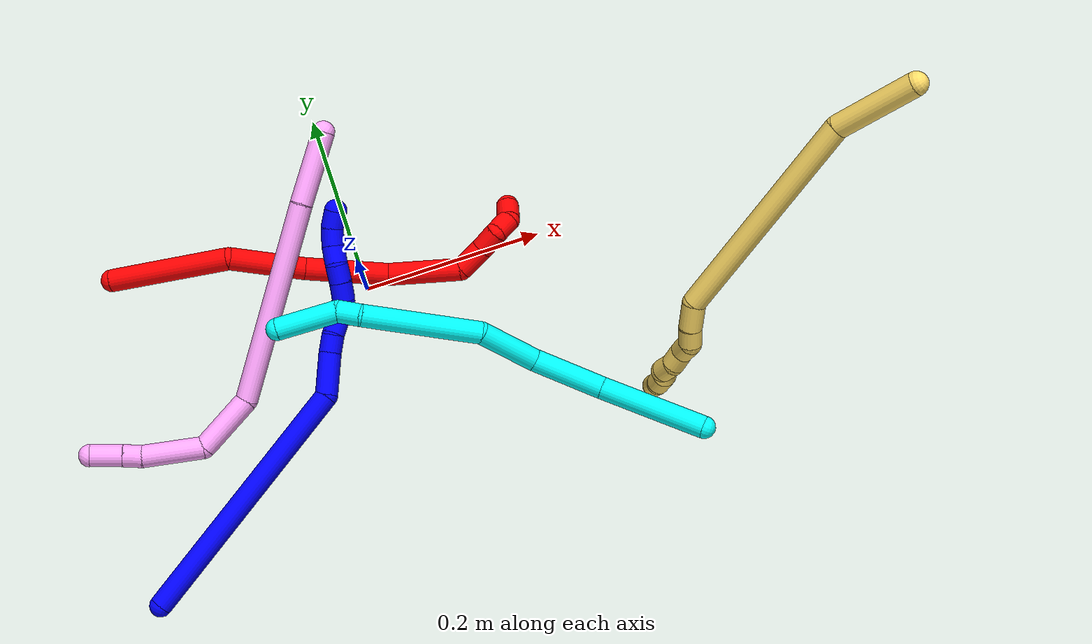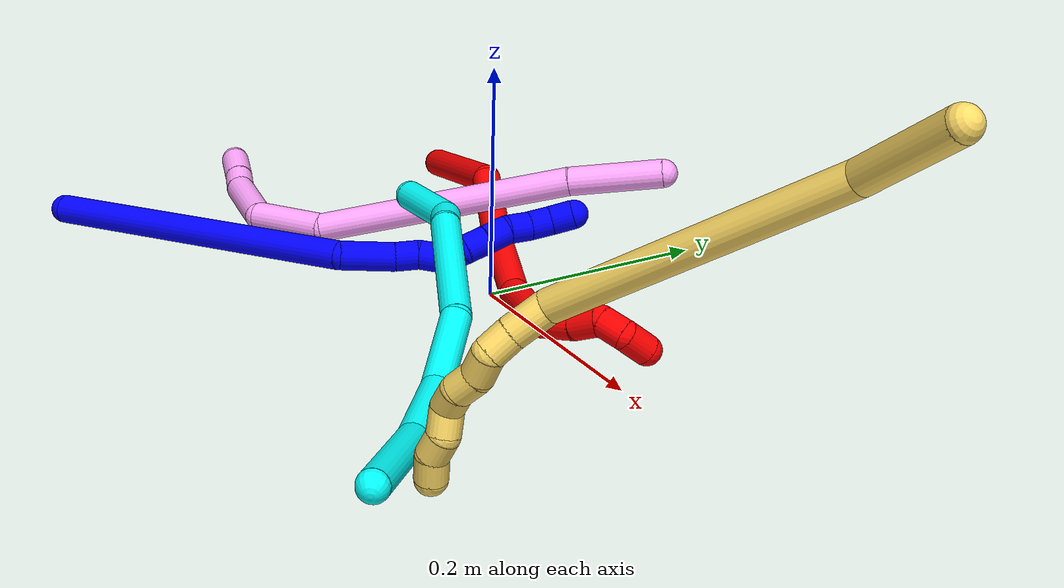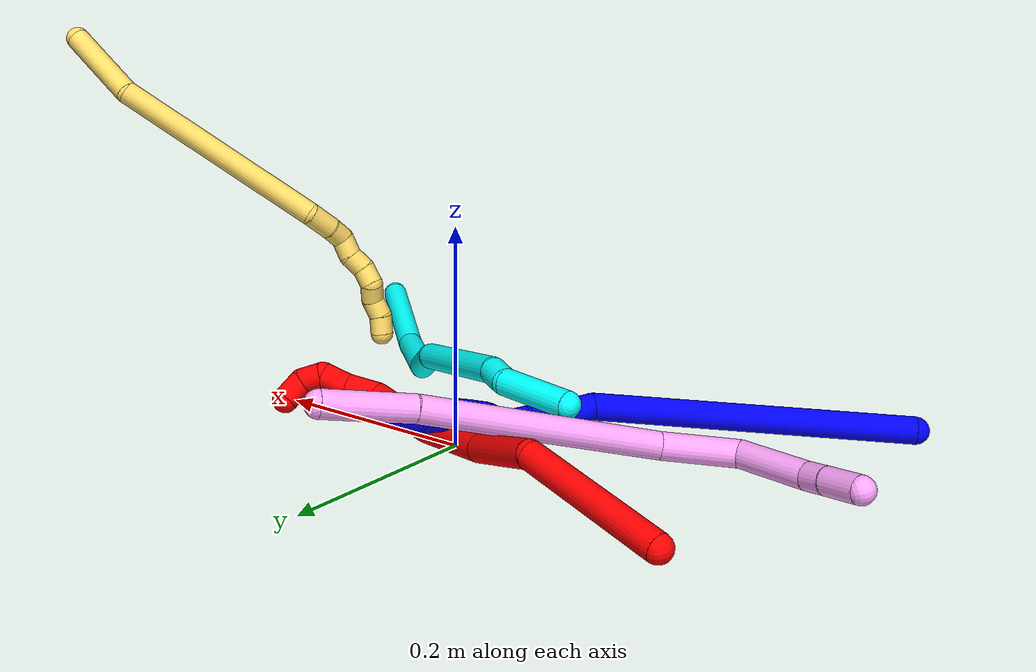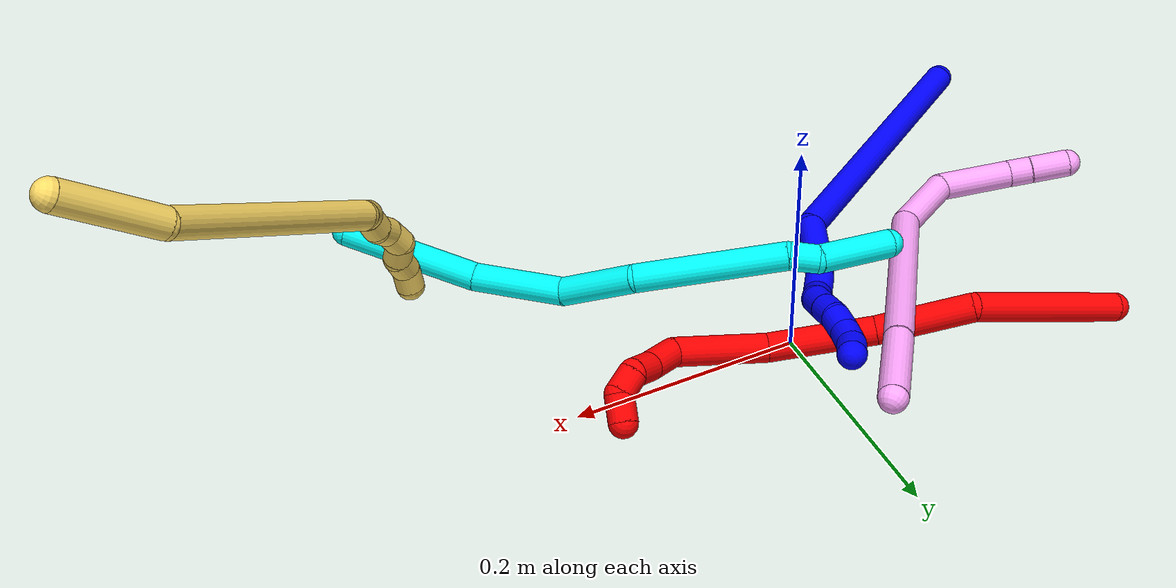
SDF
<sdf version="1.7">
 <world name="default">
  <plugin name="TubeGeneratorPlugin" filename="libtube_generator_plugin.so"/>
  <model name="photoneo_s_sensor">
   <static>1</static>
   <pose>0 0 2 1.57079 1.57079 3.14159</pose>
   <link name="link">
    <inertial><mass>0.1</mass></inertial>
    <sensor name="sensor" type="depth">
     <update_rate>30</update_rate>
     <camera>
      <horizontal_fov>1.22</horizontal_fov>
      <image><width>1920</width><height>1200</height><format>B8G8R8</format></image>
      <clip><near>0.1</near><far>4</far></clip>
      <depth_camera><output>points</output></depth_camera>
     </camera>
     <plugin name="camera_plugin" filename="libgazebo_ros_depth_camera.so">
      <baseline>0.2</baseline>
      <alwaysOn>1</alwaysOn>
      <updateRate>0.0</updateRate>
      <cameraName>camera_ir</cameraName>
      <imageTopicName>/camera/color/image_raw</imageTopicName>
      <cameraInfoTopicName>/camera/color/camera_info</cameraInfoTopicName>
      <depthImageTopicName>/camera/depth/image_raw</depthImageTopicName>
      <depthImageCameraInfoTopicName>/camera/depth/camera_info</depthImageCameraInfoTopicName>
      <pointCloudTopicName>/camera/depth/points</pointCloudTopicName>
      <frameName>fr_optical</frameName>
      <pointCloudCutoff>0.1</pointCloudCutoff>
      <pointCloudCutoffMax>2.0</pointCloudCutoffMax>
      <distortionK1>0</distortionK1>
      <distortionK2>0</distortionK2>
      <distortionK3>0</distortionK3>
      <distortionT1>0</distortionT1>
      <distortionT2>0</distortionT2>
      <CxPrime>0</CxPrime>
      <Cx>0</Cx>
      <Cy>0</Cy>
      <focalLength>0</focalLength>
      <hackBaseline>0</hackBaseline>
     </plugin>
    </sensor>
   </link>
  </model>
  <gravity>0 0 -9.8</gravity>
  <magnetic_field>6e-06 2.3e-05 -4.2e-05</magnetic_field>
  <atmosphere type="adiabatic"/>
  <physics name="default_physics" default="0" type="ode">
   <max_step_size>0.003</max_step_size>
   <real_time_factor>1</real_time_factor>
   <real_time_update_rate>1000</real_time_update_rate>
   <max_contacts>10000</max_contacts>
   <ode>
    <solver>
     <type>quick</type>
     <iters>100</iters>
     <sor>1.3</sor>
     <use_dynamic_moi_rescaling>0</use_dynamic_moi_rescaling>
    </solver>
    <constraints>
     <contact_max_correcting_vel>0</contact_max_correcting_vel>
     <contact_surface_layer>0.001</contact_surface_layer>
     <cfm>0</cfm>
     <erp>0.2</erp>
    </constraints>
   </ode>
  </physics>
  <scene><ambient>0.4 0.4 0.4 1</ambient><background>0.7 0.7 0.7 1</background><shadows>0</shadows></scene>
  <audio><device>default</device></audio>
  <spherical_coordinates>
   <surface_model>EARTH_WGS84</surface_model>
   <latitude_deg>0</latitude_deg>
   <longitude_deg>0</longitude_deg>
   <elevation>0</elevation>
   <heading_deg>0</heading_deg>
  </spherical_coordinates>
  <model name="bin">
   <static>1</static>
   <link name="bottom">
    <collision name="collision-bottom">
     <pose>0 0 -0.01 0 -0 0</pose>
     <geometry><box><size>0.8 0.6 0.02</size></box></geometry>
     <surface>
      <friction><ode><mu>100</mu><mu2>100</mu2></ode></friction>
      <contact><collide_bitmask>65535</collide_bitmask></contact>
     </surface>
    </collision>
   </link>
   <link name="west_wall">
    <collision name="collision-west_wall">
     <pose>-0.41 0 0.1 0 -0 0</pose>
     <geometry><box><size>0.02 0.6 0.2</size></box></geometry>
     <surface>
      <friction><ode><mu>100</mu><mu2>100</mu2></ode></friction>
      <contact><collide_bitmask>65535</collide_bitmask></contact>
     </surface>
    </collision>
   </link>
   <link name="east_wall">
    <collision name="collision-east_wall">
     <pose>0.41 0 0.1 0 -0 0</pose>
     <geometry><box><size>0.02 0.6 0.2</size></box></geometry>
     <surface>
      <friction><ode><mu>100</mu><mu2>100</mu2></ode></friction>
      <contact><collide_bitmask>65535</collide_bitmask></contact>
     </surface>
    </collision>
   </link>
   <link name="south_wall">
    <collision name="collision-south_wall">
     <pose>0 -0.31 0.1 0 -0 0</pose>
     <geometry><box><size>0.8 0.02 0.2</size></box></geometry>
     <surface>
      <friction><ode><mu>100</mu><mu2>100</mu2></ode></friction>
      <contact><collide_bitmask>65535</collide_bitmask></contact>
     </surface>
    </collision>
   </link>
   <link name="north_wall">
    <collision name="collision-north_wall">
     <pose>0 0.31 0.1 0 -0 0</pose>
     <geometry><box><size>0.8 0.02 0.2</size></box></geometry>
     <surface>
      <friction><ode><mu>100</mu><mu2>100</mu2></ode></friction>
      <contact><collide_bitmask>65535</collide_bitmask></contact>
     </surface>
    </collision>
   </link>
  </model>
  <model name="1">
   <static>0</static>
   <link name="1">
    <collision name="collision-cylinder-e_1_1_4">
     <pose>-0.022932 0.050946 -0.133496 -2.77702 -0.159134 0.816521</pose>
     <geometry><cylinder><radius>0.0125</radius><length>0.289432</length></cylinder></geometry>
     <surface>
      <friction><ode><mu>1.16</mu><mu2>1.16</mu2><slip1>0</slip1><slip2>0</slip2></ode></friction>
      <contact><ode><kp>1e+06</kp><kd>1</kd><max_vel>0</max_vel><min_depth>0.001</min_depth></ode></contact>
     </surface>
    </collision>
    <visual name="visual-cylinder-e_1_1_4">
     <pose>-0.022932 0.050946 -0.133496 -2.77702 -0.159134 0.816521</pose>
     <geometry><cylinder><radius>0.0125</radius><length>0.289432</length></cylinder></geometry>
     <material><ambient>0 0 1 1</ambient></material>
    </visual>
    <collision name="collision-cylinder-e_2_4_5">
     <pose>-0.035477 0.109776 -0.286963 -2.76558 0.450612 -1.75595</pose>
     <geometry><cylinder><radius>0.0125</radius><length>0.047702</length></cylinder></geometry>
     <surface>
      <friction><ode><mu>1.16</mu><mu2>1.16</mu2><slip1>0</slip1><slip2>0</slip2></ode></friction>
      <contact><ode><kp>1e+06</kp><kd>1</kd><max_vel>0</max_vel><min_depth>0.001</min_depth></ode></contact>
     </surface>
    </collision>
    <visual name="visual-cylinder-e_2_4_5">
     <pose>-0.035477 0.109776 -0.286963 -2.76558 0.450612 -1.75595</pose>
     <geometry><cylinder><radius>0.0125</radius><length>0.047702</length></cylinder></geometry>
     <material><ambient>0 0 1 1</ambient></material>
    </visual>
    <collision name="collision-cylinder-e_3_5_6">
     <pose>-0.021818 0.11973 -0.316523 -2.92908 0.321829 -1.97892</pose>
     <geometry><cylinder><radius>0.0125</radius><length>0.020684</length></cylinder></geometry>
     <surface>
      <friction><ode><mu>1.16</mu><mu2>1.16</mu2><slip1>0</slip1><slip2>0</slip2></ode></friction>
      <contact><ode><kp>1e+06</kp><kd>1</kd><max_vel>0</max_vel><min_depth>0.001</min_depth></ode></contact>
     </surface>
    </collision>
    <visual name="visual-cylinder-e_3_5_6">
     <pose>-0.021818 0.11973 -0.316523 -2.92908 0.321829 -1.97892</pose>
     <geometry><cylinder><radius>0.0125</radius><length>0.020684</length></cylinder></geometry>
     <material><ambient>0 0 1 1</ambient></material>
    </visual>
    <collision name="collision-cylinder-e_4_6_7">
     <pose>-0.016069 0.126572 -0.335562 -2.67384 0.229915 -0.902623</pose>
     <geometry><cylinder><radius>0.0125</radius><length>0.021742</length></cylinder></geometry>
     <surface>
      <friction><ode><mu>1.16</mu><mu2>1.16</mu2><slip1>0</slip1><slip2>0</slip2></ode></friction>
      <contact><ode><kp>1e+06</kp><kd>1</kd><max_vel>0</max_vel><min_depth>0.001</min_depth></ode></contact>
     </surface>
    </collision>
    <visual name="visual-cylinder-e_4_6_7">
     <pose>-0.016069 0.126572 -0.335562 -2.67384 0.229915 -0.902623</pose>
     <geometry><cylinder><radius>0.0125</radius><length>0.021742</length></cylinder></geometry>
     <material><ambient>0 0 1 1</ambient></material>
    </visual>
    <collision name="collision-cylinder-e_5_7_8">
     <pose>-0.012726 0.129906 -0.354961 2.99803 0.085898 1.07739</pose>
     <geometry><cylinder><radius>0.0125</radius><length>0.020183</length></cylinder></geometry>
     <surface>
      <friction><ode><mu>1.16</mu><mu2>1.16</mu2><slip1>0</slip1><slip2>0</slip2></ode></friction>
      <contact><ode><kp>1e+06</kp><kd>1</kd><max_vel>0</max_vel><min_depth>0.001</min_depth></ode></contact>
     </surface>
    </collision>
    <visual name="visual-cylinder-e_5_7_8">
     <pose>-0.012726 0.129906 -0.354961 2.99803 0.085898 1.07739</pose>
     <geometry><cylinder><radius>0.0125</radius><length>0.020183</length></cylinder></geometry>
     <material><ambient>0 0 1 1</ambient></material>
    </visual>
    <collision name="collision-cylinder-e_6_8_9">
     <pose>-0.006566 0.127258 -0.373424 3.00046 0.551915 2.65237</pose>
     <geometry><cylinder><radius>0.0125</radius><length>0.020194</length></cylinder></geometry>
     <surface>
      <friction><ode><mu>1.16</mu><mu2>1.16</mu2><slip1>0</slip1><slip2>0</slip2></ode></friction>
      <contact><ode><kp>1e+06</kp><kd>1</kd><max_vel>0</max_vel><min_depth>0.001</min_depth></ode></contact>
     </surface>
    </collision>
    <visual name="visual-cylinder-e_6_8_9">
     <pose>-0.006566 0.127258 -0.373424 3.00046 0.551915 2.65237</pose>
     <geometry><cylinder><radius>0.0125</radius><length>0.020194</length></cylinder></geometry>
     <material><ambient>0 0 1 1</ambient></material>
    </visual>
    <collision name="collision-cylinder-e_7_9_10">
     <pose>0.0045 0.124836 -0.390039 2.99302 0.61375 2.68025</pose>
     <geometry><cylinder><radius>0.0125</radius><length>0.020044</length></cylinder></geometry>
     <surface>
      <friction><ode><mu>1.16</mu><mu2>1.16</mu2><slip1>0</slip1><slip2>0</slip2></ode></friction>
      <contact><ode><kp>1e+06</kp><kd>1</kd><max_vel>0</max_vel><min_depth>0.001</min_depth></ode></contact>
     </surface>
    </collision>
    <visual name="visual-cylinder-e_7_9_10">
     <pose>0.0045 0.124836 -0.390039 2.99302 0.61375 2.68025</pose>
     <geometry><cylinder><radius>0.0125</radius><length>0.020044</length></cylinder></geometry>
     <material><ambient>0 0 1 1</ambient></material>
    </visual>
    <collision name="collision-cylinder-e_8_10_11">
     <pose>0.016633 0.125259 -0.405693 -2.92821 0.688797 -2.56128</pose>
     <geometry><cylinder><radius>0.0125</radius><length>0.020017</length></cylinder></geometry>
     <surface>
      <friction><ode><mu>1.16</mu><mu2>1.16</mu2><slip1>0</slip1><slip2>0</slip2></ode></friction>
      <contact><ode><kp>1e+06</kp><kd>1</kd><max_vel>0</max_vel><min_depth>0.001</min_depth></ode></contact>
     </surface>
    </collision>
    <visual name="visual-cylinder-e_8_10_11">
     <pose>0.016633 0.125259 -0.405693 -2.92821 0.688797 -2.56128</pose>
     <geometry><cylinder><radius>0.0125</radius><length>0.020017</length></cylinder></geometry>
     <material><ambient>0 0 1 1</ambient></material>
    </visual>
    <collision name="collision-cylinder-e_9_11_12">
     <pose>0.027886 0.127547 -0.421943 -3.06688 0.511095 -2.85742</pose>
     <geometry><cylinder><radius>0.0125</radius><length>0.020002</length></cylinder></geometry>
     <surface>
      <friction><ode><mu>1.16</mu><mu2>1.16</mu2><slip1>0</slip1><slip2>0</slip2></ode></friction>
      <contact><ode><kp>1e+06</kp><kd>1</kd><max_vel>0</max_vel><min_depth>0.001</min_depth></ode></contact>
     </surface>
    </collision>
    <visual name="visual-cylinder-e_9_11_12">
     <pose>0.027886 0.127547 -0.421943 -3.06688 0.511095 -2.85742</pose>
     <geometry><cylinder><radius>0.0125</radius><length>0.020002</length></cylinder></geometry>
     <material><ambient>0 0 1 1</ambient></material>
    </visual>
    <collision name="collision-cylinder-e_10_12_2">
     <pose>0.034927 0.128348 -0.440407 -3.1262 0.216591 -3.00026</pose>
     <geometry><cylinder><radius>0.0125</radius><length>0.020001</length></cylinder></geometry>
     <surface>
      <friction><ode><mu>1.16</mu><mu2>1.16</mu2><slip1>0</slip1><slip2>0</slip2></ode></friction>
      <contact><ode><kp>1e+06</kp><kd>1</kd><max_vel>0</max_vel><min_depth>0.001</min_depth></ode></contact>
     </surface>
    </collision>
    <visual name="visual-cylinder-e_10_12_2">
     <pose>0.034927 0.128348 -0.440407 -3.1262 0.216591 -3.00026</pose>
     <geometry><cylinder><radius>0.0125</radius><length>0.020001</length></cylinder></geometry>
     <material><ambient>0 0 1 1</ambient></material>
    </visual>
    <collision name="collision-sphere-2">
     <pose>0.037076 0.128498 -0.450172 0 -0 0</pose>
     <geometry><sphere><radius>0.0125</radius></sphere></geometry>
     <surface>
      <friction><ode><mu>1.16</mu><mu2>1.16</mu2><slip1>0</slip1><slip2>0</slip2></ode></friction>
      <contact><ode><kp>1e+06</kp><kd>1</kd><max_vel>0</max_vel><min_depth>0.001</min_depth></ode></contact>
     </surface>
    </collision>
    <visual name="visual-sphere-2">
     <pose>0.037076 0.128498 -0.450172 0 -0 0</pose>
     <geometry><sphere><radius>0.0125</radius></sphere></geometry>
     <material><ambient>0 0 1 1</ambient></material>
    </visual>
    <collision name="collision-sphere-12">
     <pose>0.032778 0.128198 -0.430641 0 -0 0</pose>
     <geometry><sphere><radius>0.0125</radius></sphere></geometry>
     <surface>
      <friction><ode><mu>1.16</mu><mu2>1.16</mu2><slip1>0</slip1><slip2>0</slip2></ode></friction>
      <contact><ode><kp>1e+06</kp><kd>1</kd><max_vel>0</max_vel><min_depth>0.001</min_depth></ode></contact>
     </surface>
    </collision>
    <visual name="visual-sphere-12">
     <pose>0.032778 0.128198 -0.430641 0 -0 0</pose>
     <geometry><sphere><radius>0.0125</radius></sphere></geometry>
     <material><ambient>0 0 1 1</ambient></material>
    </visual>
    <collision name="collision-sphere-11">
     <pose>0.022994 0.126896 -0.413244 0 -0 0</pose>
     <geometry><sphere><radius>0.0125</radius></sphere></geometry>
     <surface>
      <friction><ode><mu>1.16</mu><mu2>1.16</mu2><slip1>0</slip1><slip2>0</slip2></ode></friction>
      <contact><ode><kp>1e+06</kp><kd>1</kd><max_vel>0</max_vel><min_depth>0.001</min_depth></ode></contact>
     </surface>
    </collision>
    <visual name="visual-sphere-11">
     <pose>0.022994 0.126896 -0.413244 0 -0 0</pose>
     <geometry><sphere><radius>0.0125</radius></sphere></geometry>
     <material><ambient>0 0 1 1</ambient></material>
    </visual>
    <collision name="collision-sphere-10">
     <pose>0.010272 0.123623 -0.398141 0 -0 0</pose>
     <geometry><sphere><radius>0.0125</radius></sphere></geometry>
     <surface>
      <friction><ode><mu>1.16</mu><mu2>1.16</mu2><slip1>0</slip1><slip2>0</slip2></ode></friction>
      <contact><ode><kp>1e+06</kp><kd>1</kd><max_vel>0</max_vel><min_depth>0.001</min_depth></ode></contact>
     </surface>
    </collision>
    <visual name="visual-sphere-10">
     <pose>0.010272 0.123623 -0.398141 0 -0 0</pose>
     <geometry><sphere><radius>0.0125</radius></sphere></geometry>
     <material><ambient>0 0 1 1</ambient></material>
    </visual>
    <collision name="collision-sphere-9">
     <pose>-0.001272 0.126048 -0.381936 0 -0 0</pose>
     <geometry><sphere><radius>0.0125</radius></sphere></geometry>
     <surface>
      <friction><ode><mu>1.16</mu><mu2>1.16</mu2><slip1>0</slip1><slip2>0</slip2></ode></friction>
      <contact><ode><kp>1e+06</kp><kd>1</kd><max_vel>0</max_vel><min_depth>0.001</min_depth></ode></contact>
     </surface>
    </collision>
    <visual name="visual-sphere-9">
     <pose>-0.001272 0.126048 -0.381936 0 -0 0</pose>
     <geometry><sphere><radius>0.0125</radius></sphere></geometry>
     <material><ambient>0 0 1 1</ambient></material>
    </visual>
    <collision name="collision-sphere-4">
     <pose>-0.045864 0.101892 -0.266993 0 -0 0</pose>
     <geometry><sphere><radius>0.0125</radius></sphere></geometry>
     <surface>
      <friction><ode><mu>1.16</mu><mu2>1.16</mu2><slip1>0</slip1><slip2>0</slip2></ode></friction>
      <contact><ode><kp>1e+06</kp><kd>1</kd><max_vel>0</max_vel><min_depth>0.001</min_depth></ode></contact>
     </surface>
    </collision>
    <visual name="visual-sphere-4">
     <pose>-0.045864 0.101892 -0.266993 0 -0 0</pose>
     <geometry><sphere><radius>0.0125</radius></sphere></geometry>
     <material><ambient>0 0 1 1</ambient></material>
    </visual>
    <collision name="collision-sphere-1">
     <geometry><sphere><radius>0.0125</radius></sphere></geometry>
     <surface>
      <friction><ode><mu>1.16</mu><mu2>1.16</mu2><slip1>0</slip1><slip2>0</slip2></ode></friction>
      <contact><ode><kp>1e+06</kp><kd>1</kd><max_vel>0</max_vel><min_depth>0.001</min_depth></ode></contact>
     </surface>
    </collision>
    <visual name="visual-sphere-1">
     <geometry><sphere><radius>0.0125</radius></sphere></geometry>
     <material><ambient>0 0 1 1</ambient></material>
    </visual>
    <collision name="collision-sphere-8">
     <pose>-0.01186 0.128467 -0.364912 0 -0 0</pose>
     <geometry><sphere><radius>0.0125</radius></sphere></geometry>
     <surface>
      <friction><ode><mu>1.16</mu><mu2>1.16</mu2><slip1>0</slip1><slip2>0</slip2></ode></friction>
      <contact><ode><kp>1e+06</kp><kd>1</kd><max_vel>0</max_vel><min_depth>0.001</min_depth></ode></contact>
     </surface>
    </collision>
    <visual name="visual-sphere-8">
     <pose>-0.01186 0.128467 -0.364912 0 -0 0</pose>
     <geometry><sphere><radius>0.0125</radius></sphere></geometry>
     <material><ambient>0 0 1 1</ambient></material>
    </visual>
    <collision name="collision-sphere-5">
     <pose>-0.025089 0.117661 -0.306933 0 -0 0</pose>
     <geometry><sphere><radius>0.0125</radius></sphere></geometry>
     <surface>
      <friction><ode><mu>1.16</mu><mu2>1.16</mu2><slip1>0</slip1><slip2>0</slip2></ode></friction>
      <contact><ode><kp>1e+06</kp><kd>1</kd><max_vel>0</max_vel><min_depth>0.001</min_depth></ode></contact>
     </surface>
    </collision>
    <visual name="visual-sphere-5">
     <pose>-0.025089 0.117661 -0.306933 0 -0 0</pose>
     <geometry><sphere><radius>0.0125</radius></sphere></geometry>
     <material><ambient>0 0 1 1</ambient></material>
    </visual>
    <collision name="collision-sphere-6">
     <pose>-0.018547 0.121799 -0.326114 0 -0 0</pose>
     <geometry><sphere><radius>0.0125</radius></sphere></geometry>
     <surface>
      <friction><ode><mu>1.16</mu><mu2>1.16</mu2><slip1>0</slip1><slip2>0</slip2></ode></friction>
      <contact><ode><kp>1e+06</kp><kd>1</kd><max_vel>0</max_vel><min_depth>0.001</min_depth></ode></contact>
     </surface>
    </collision>
    <visual name="visual-sphere-6">
     <pose>-0.018547 0.121799 -0.326114 0 -0 0</pose>
     <geometry><sphere><radius>0.0125</radius></sphere></geometry>
     <material><ambient>0 0 1 1</ambient></material>
    </visual>
    <collision name="collision-sphere-7">
     <pose>-0.013592 0.131344 -0.34501 0 -0 0</pose>
     <geometry><sphere><radius>0.0125</radius></sphere></geometry>
     <surface>
      <friction><ode><mu>1.16</mu><mu2>1.16</mu2><slip1>0</slip1><slip2>0</slip2></ode></friction>
      <contact><ode><kp>1e+06</kp><kd>1</kd><max_vel>0</max_vel><min_depth>0.001</min_depth></ode></contact>
     </surface>
    </collision>
    <visual name="visual-sphere-7">
     <pose>-0.013592 0.131344 -0.34501 0 -0 0</pose>
     <geometry><sphere><radius>0.0125</radius></sphere></geometry>
     <material><ambient>0 0 1 1</ambient></material>
    </visual>
    <inertial>
     <pose>-0.01568 0.08106 -0.228123 0 -0 0</pose>
     <mass>0.5</mass>
     <inertia>
      <ixx>0.002821</ixx>
      <ixy>0</ixy>
      <ixz>0</ixz>
      <iyy>0.000254</iyy>
      <iyz>0</iyz>
      <izz>-0.000442</izz>
     </inertia>
    </inertial>
   </link>
   <pose>-0.319661 -0.262077 0.012492 -1.95477 0.185351 2.30877</pose>
  </model>
  <model name="2">
   <static>0</static>
   <link name="2">
    <collision name="collision-cylinder-e_1_1_4">
     <pose>0.067022 -0.017143 0.006662 1.20014 1.30297 0.961819</pose>
     <geometry><cylinder><radius>0.0125</radius><length>0.138999</length></cylinder></geometry>
     <surface>
      <friction><ode><mu>1.16</mu><mu2>1.16</mu2><slip1>0</slip1><slip2>0</slip2></ode></friction>
      <contact><ode><kp>1e+06</kp><kd>1</kd><max_vel>0</max_vel><min_depth>0.001</min_depth></ode></contact>
     </surface>
    </collision>
    <visual name="visual-cylinder-e_1_1_4">
     <pose>0.067022 -0.017143 0.006662 1.20014 1.30297 0.961819</pose>
     <geometry><cylinder><radius>0.0125</radius><length>0.138999</length></cylinder></geometry>
     <material><ambient>1 0 0 1</ambient></material>
    </visual>
    <collision name="collision-cylinder-e_2_4_5">
     <pose>0.169961 -0.045773 -0.005304 2.58901 1.02355 2.20663</pose>
     <geometry><cylinder><radius>0.0125</radius><length>0.084119</length></cylinder></geometry>
     <surface>
      <friction><ode><mu>1.16</mu><mu2>1.16</mu2><slip1>0</slip1><slip2>0</slip2></ode></friction>
      <contact><ode><kp>1e+06</kp><kd>1</kd><max_vel>0</max_vel><min_depth>0.001</min_depth></ode></contact>
     </surface>
    </collision>
    <visual name="visual-cylinder-e_2_4_5">
     <pose>0.169961 -0.045773 -0.005304 2.58901 1.02355 2.20663</pose>
     <geometry><cylinder><radius>0.0125</radius><length>0.084119</length></cylinder></geometry>
     <material><ambient>1 0 0 1</ambient></material>
    </visual>
    <collision name="collision-cylinder-e_3_5_6">
     <pose>0.247868 -0.070905 -0.038327 2.38294 1.12952 2.01842</pose>
     <geometry><cylinder><radius>0.0125</radius><length>0.092877</length></cylinder></geometry>
     <surface>
      <friction><ode><mu>1.16</mu><mu2>1.16</mu2><slip1>0</slip1><slip2>0</slip2></ode></friction>
      <contact><ode><kp>1e+06</kp><kd>1</kd><max_vel>0</max_vel><min_depth>0.001</min_depth></ode></contact>
     </surface>
    </collision>
    <visual name="visual-cylinder-e_3_5_6">
     <pose>0.247868 -0.070905 -0.038327 2.38294 1.12952 2.01842</pose>
     <geometry><cylinder><radius>0.0125</radius><length>0.092877</length></cylinder></geometry>
     <material><ambient>1 0 0 1</ambient></material>
    </visual>
    <collision name="collision-cylinder-e_4_6_7">
     <pose>0.328749 -0.096379 -0.054747 1.74035 1.27147 1.43767</pose>
     <geometry><cylinder><radius>0.0125</radius><length>0.081401</length></cylinder></geometry>
     <surface>
      <friction><ode><mu>1.16</mu><mu2>1.16</mu2><slip1>0</slip1><slip2>0</slip2></ode></friction>
      <contact><ode><kp>1e+06</kp><kd>1</kd><max_vel>0</max_vel><min_depth>0.001</min_depth></ode></contact>
     </surface>
    </collision>
    <visual name="visual-cylinder-e_4_6_7">
     <pose>0.328749 -0.096379 -0.054747 1.74035 1.27147 1.43767</pose>
     <geometry><cylinder><radius>0.0125</radius><length>0.081401</length></cylinder></geometry>
     <material><ambient>1 0 0 1</ambient></material>
    </visual>
    <collision name="collision-cylinder-e_5_7_8">
     <pose>0.382092 -0.103239 -0.052442 -0.854153 1.1429 -0.569361</pose>
     <geometry><cylinder><radius>0.0125</radius><length>0.031769</length></cylinder></geometry>
     <surface>
      <friction><ode><mu>1.16</mu><mu2>1.16</mu2><slip1>0</slip1><slip2>0</slip2></ode></friction>
      <contact><ode><kp>1e+06</kp><kd>1</kd><max_vel>0</max_vel><min_depth>0.001</min_depth></ode></contact>
     </surface>
    </collision>
    <visual name="visual-cylinder-e_5_7_8">
     <pose>0.382092 -0.103239 -0.052442 -0.854153 1.1429 -0.569361</pose>
     <geometry><cylinder><radius>0.0125</radius><length>0.031769</length></cylinder></geometry>
     <material><ambient>1 0 0 1</ambient></material>
    </visual>
    <collision name="collision-cylinder-e_6_8_9">
     <pose>0.407235 -0.094986 -0.042262 -0.511318 1.01041 -0.287137</pose>
     <geometry><cylinder><radius>0.0125</radius><length>0.025243</length></cylinder></geometry>
     <surface>
      <friction><ode><mu>1.16</mu><mu2>1.16</mu2><slip1>0</slip1><slip2>0</slip2></ode></friction>
      <contact><ode><kp>1e+06</kp><kd>1</kd><max_vel>0</max_vel><min_depth>0.001</min_depth></ode></contact>
     </surface>
    </collision>
    <visual name="visual-cylinder-e_6_8_9">
     <pose>0.407235 -0.094986 -0.042262 -0.511318 1.01041 -0.287137</pose>
     <geometry><cylinder><radius>0.0125</radius><length>0.025243</length></cylinder></geometry>
     <material><ambient>1 0 0 1</ambient></material>
    </visual>
    <collision name="collision-cylinder-e_7_9_10">
     <pose>0.42667 -0.085641 -0.038707 -1.93278 0.932846 -1.25986</pose>
     <geometry><cylinder><radius>0.0125</radius><length>0.021769</length></cylinder></geometry>
     <surface>
      <friction><ode><mu>1.16</mu><mu2>1.16</mu2><slip1>0</slip1><slip2>0</slip2></ode></friction>
      <contact><ode><kp>1e+06</kp><kd>1</kd><max_vel>0</max_vel><min_depth>0.001</min_depth></ode></contact>
     </surface>
    </collision>
    <visual name="visual-cylinder-e_7_9_10">
     <pose>0.42667 -0.085641 -0.038707 -1.93278 0.932846 -1.25986</pose>
     <geometry><cylinder><radius>0.0125</radius><length>0.021769</length></cylinder></geometry>
     <material><ambient>1 0 0 1</ambient></material>
    </visual>
    <collision name="collision-cylinder-e_8_10_2">
     <pose>0.437637 -0.068612 -0.045085 -1.92711 0.187806 -0.269449</pose>
     <geometry><cylinder><radius>0.0125</radius><length>0.023823</length></cylinder></geometry>
     <surface>
      <friction><ode><mu>1.16</mu><mu2>1.16</mu2><slip1>0</slip1><slip2>0</slip2></ode></friction>
      <contact><ode><kp>1e+06</kp><kd>1</kd><max_vel>0</max_vel><min_depth>0.001</min_depth></ode></contact>
     </surface>
    </collision>
    <visual name="visual-cylinder-e_8_10_2">
     <pose>0.437637 -0.068612 -0.045085 -1.92711 0.187806 -0.269449</pose>
     <geometry><cylinder><radius>0.0125</radius><length>0.023823</length></cylinder></geometry>
     <material><ambient>1 0 0 1</ambient></material>
    </visual>
    <collision name="collision-sphere-2">
     <pose>0.439861 -0.057645 -0.049167 0 -0 0</pose>
     <geometry><sphere><radius>0.0125</radius></sphere></geometry>
     <surface>
      <friction><ode><mu>1.16</mu><mu2>1.16</mu2><slip1>0</slip1><slip2>0</slip2></ode></friction>
      <contact><ode><kp>1e+06</kp><kd>1</kd><max_vel>0</max_vel><min_depth>0.001</min_depth></ode></contact>
     </surface>
    </collision>
    <visual name="visual-sphere-2">
     <pose>0.439861 -0.057645 -0.049167 0 -0 0</pose>
     <geometry><sphere><radius>0.0125</radius></sphere></geometry>
     <material><ambient>1 0 0 1</ambient></material>
    </visual>
    <collision name="collision-sphere-10">
     <pose>0.435413 -0.079579 -0.041003 0 -0 0</pose>
     <geometry><sphere><radius>0.0125</radius></sphere></geometry>
     <surface>
      <friction><ode><mu>1.16</mu><mu2>1.16</mu2><slip1>0</slip1><slip2>0</slip2></ode></friction>
      <contact><ode><kp>1e+06</kp><kd>1</kd><max_vel>0</max_vel><min_depth>0.001</min_depth></ode></contact>
     </surface>
    </collision>
    <visual name="visual-sphere-10">
     <pose>0.435413 -0.079579 -0.041003 0 -0 0</pose>
     <geometry><sphere><radius>0.0125</radius></sphere></geometry>
     <material><ambient>1 0 0 1</ambient></material>
    </visual>
    <collision name="collision-sphere-9">
     <pose>0.417926 -0.091703 -0.036412 0 -0 0</pose>
     <geometry><sphere><radius>0.0125</radius></sphere></geometry>
     <surface>
      <friction><ode><mu>1.16</mu><mu2>1.16</mu2><slip1>0</slip1><slip2>0</slip2></ode></friction>
      <contact><ode><kp>1e+06</kp><kd>1</kd><max_vel>0</max_vel><min_depth>0.001</min_depth></ode></contact>
     </surface>
    </collision>
    <visual name="visual-sphere-9">
     <pose>0.417926 -0.091703 -0.036412 0 -0 0</pose>
     <geometry><sphere><radius>0.0125</radius></sphere></geometry>
     <material><ambient>1 0 0 1</ambient></material>
    </visual>
    <collision name="collision-sphere-4">
     <pose>0.134044 -0.034286 0.013324 0 -0 0</pose>
     <geometry><sphere><radius>0.0125</radius></sphere></geometry>
     <surface>
      <friction><ode><mu>1.16</mu><mu2>1.16</mu2><slip1>0</slip1><slip2>0</slip2></ode></friction>
      <contact><ode><kp>1e+06</kp><kd>1</kd><max_vel>0</max_vel><min_depth>0.001</min_depth></ode></contact>
     </surface>
    </collision>
    <visual name="visual-sphere-4">
     <pose>0.134044 -0.034286 0.013324 0 -0 0</pose>
     <geometry><sphere><radius>0.0125</radius></sphere></geometry>
     <material><ambient>1 0 0 1</ambient></material>
    </visual>
    <collision name="collision-sphere-1">
     <geometry><sphere><radius>0.0125</radius></sphere></geometry>
     <surface>
      <friction><ode><mu>1.16</mu><mu2>1.16</mu2><slip1>0</slip1><slip2>0</slip2></ode></friction>
      <contact><ode><kp>1e+06</kp><kd>1</kd><max_vel>0</max_vel><min_depth>0.001</min_depth></ode></contact>
     </surface>
    </collision>
    <visual name="visual-sphere-1">
     <geometry><sphere><radius>0.0125</radius></sphere></geometry>
     <material><ambient>1 0 0 1</ambient></material>
    </visual>
    <collision name="collision-sphere-8">
     <pose>0.396544 -0.098269 -0.048113 0 -0 0</pose>
     <geometry><sphere><radius>0.0125</radius></sphere></geometry>
     <surface>
      <friction><ode><mu>1.16</mu><mu2>1.16</mu2><slip1>0</slip1><slip2>0</slip2></ode></friction>
      <contact><ode><kp>1e+06</kp><kd>1</kd><max_vel>0</max_vel><min_depth>0.001</min_depth></ode></contact>
     </surface>
    </collision>
    <visual name="visual-sphere-8">
     <pose>0.396544 -0.098269 -0.048113 0 -0 0</pose>
     <geometry><sphere><radius>0.0125</radius></sphere></geometry>
     <material><ambient>1 0 0 1</ambient></material>
    </visual>
    <collision name="collision-sphere-5">
     <pose>0.205878 -0.05726 -0.023932 0 -0 0</pose>
     <geometry><sphere><radius>0.0125</radius></sphere></geometry>
     <surface>
      <friction><ode><mu>1.16</mu><mu2>1.16</mu2><slip1>0</slip1><slip2>0</slip2></ode></friction>
      <contact><ode><kp>1e+06</kp><kd>1</kd><max_vel>0</max_vel><min_depth>0.001</min_depth></ode></contact>
     </surface>
    </collision>
    <visual name="visual-sphere-5">
     <pose>0.205878 -0.05726 -0.023932 0 -0 0</pose>
     <geometry><sphere><radius>0.0125</radius></sphere></geometry>
     <material><ambient>1 0 0 1</ambient></material>
    </visual>
    <collision name="collision-sphere-6">
     <pose>0.289858 -0.08455 -0.052721 0 -0 0</pose>
     <geometry><sphere><radius>0.0125</radius></sphere></geometry>
     <surface>
      <friction><ode><mu>1.16</mu><mu2>1.16</mu2><slip1>0</slip1><slip2>0</slip2></ode></friction>
      <contact><ode><kp>1e+06</kp><kd>1</kd><max_vel>0</max_vel><min_depth>0.001</min_depth></ode></contact>
     </surface>
    </collision>
    <visual name="visual-sphere-6">
     <pose>0.289858 -0.08455 -0.052721 0 -0 0</pose>
     <geometry><sphere><radius>0.0125</radius></sphere></geometry>
     <material><ambient>1 0 0 1</ambient></material>
    </visual>
    <collision name="collision-sphere-7">
     <pose>0.36764 -0.108209 -0.056772 0 -0 0</pose>
     <geometry><sphere><radius>0.0125</radius></sphere></geometry>
     <surface>
      <friction><ode><mu>1.16</mu><mu2>1.16</mu2><slip1>0</slip1><slip2>0</slip2></ode></friction>
      <contact><ode><kp>1e+06</kp><kd>1</kd><max_vel>0</max_vel><min_depth>0.001</min_depth></ode></contact>
     </surface>
    </collision>
    <visual name="visual-sphere-7">
     <pose>0.36764 -0.108209 -0.056772 0 -0 0</pose>
     <geometry><sphere><radius>0.0125</radius></sphere></geometry>
     <material><ambient>1 0 0 1</ambient></material>
    </visual>
    <inertial>
     <pose>0.231054 -0.059681 -0.024372 0 -0 0</pose>
     <mass>0.5</mass>
     <inertia>
      <ixx>0.000157</ixx>
      <ixy>0</ixy>
      <ixz>0</ixz>
      <iyy>0.00048</iyy>
      <iyz>0</iyz>
      <izz>-0.000286</izz>
     </inertia>
    </inertial>
   </link>
   <pose>-0.265641 0.09647 0.011497 -0.354569 -0.069166 0.027793</pose>
  </model>
  <model name="3">
   <static>0</static>
   <link name="3">
    <collision name="collision-cylinder-e_1_1_4">
     <pose>-0.026768 -0.00228 -0.054024 3.09941 -0.459675 -2.96178</pose>
     <geometry><cylinder><radius>0.0125</radius><length>0.12067</length></cylinder></geometry>
     <surface>
      <friction><ode><mu>1.16</mu><mu2>1.16</mu2><slip1>0</slip1><slip2>0</slip2></ode></friction>
      <contact><ode><kp>1e+06</kp><kd>1</kd><max_vel>0</max_vel><min_depth>0.001</min_depth></ode></contact>
     </surface>
    </collision>
    <visual name="visual-cylinder-e_1_1_4">
     <pose>-0.026768 -0.00228 -0.054024 3.09941 -0.459675 -2.96178</pose>
     <geometry><cylinder><radius>0.0125</radius><length>0.12067</length></cylinder></geometry>
     <material><ambient>0.003922 1 0.996078 1</ambient></material>
    </visual>
    <collision name="collision-cylinder-e_2_4_5">
     <pose>-0.062821 -0.006973 -0.147332 3.08026 -0.231665 -2.62602</pose>
     <geometry><cylinder><radius>0.0125</radius><length>0.080879</length></cylinder></geometry>
     <surface>
      <friction><ode><mu>1.16</mu><mu2>1.16</mu2><slip1>0</slip1><slip2>0</slip2></ode></friction>
      <contact><ode><kp>1e+06</kp><kd>1</kd><max_vel>0</max_vel><min_depth>0.001</min_depth></ode></contact>
     </surface>
    </collision>
    <visual name="visual-cylinder-e_2_4_5">
     <pose>-0.062821 -0.006973 -0.147332 3.08026 -0.231665 -2.62602</pose>
     <geometry><cylinder><radius>0.0125</radius><length>0.080879</length></cylinder></geometry>
     <material><ambient>0.003922 1 0.996078 1</ambient></material>
    </visual>
    <collision name="collision-cylinder-e_3_5_6">
     <pose>-0.065086 -0.013729 -0.221105 3.01629 0.199267 2.02075</pose>
     <geometry><cylinder><radius>0.0125</radius><length>0.070924</length></cylinder></geometry>
     <surface>
      <friction><ode><mu>1.16</mu><mu2>1.16</mu2><slip1>0</slip1><slip2>0</slip2></ode></friction>
      <contact><ode><kp>1e+06</kp><kd>1</kd><max_vel>0</max_vel><min_depth>0.001</min_depth></ode></contact>
     </surface>
    </collision>
    <visual name="visual-cylinder-e_3_5_6">
     <pose>-0.065086 -0.013729 -0.221105 3.01629 0.199267 2.02075</pose>
     <geometry><cylinder><radius>0.0125</radius><length>0.070924</length></cylinder></geometry>
     <material><ambient>0.003922 1 0.996078 1</ambient></material>
    </visual>
    <collision name="collision-cylinder-e_4_6_7">
     <pose>-0.060006 -0.005666 -0.320783 -2.95352 -0.029225 0.307458</pose>
     <geometry><cylinder><radius>0.0125</radius><length>0.132777</length></cylinder></geometry>
     <surface>
      <friction><ode><mu>1.16</mu><mu2>1.16</mu2><slip1>0</slip1><slip2>0</slip2></ode></friction>
      <contact><ode><kp>1e+06</kp><kd>1</kd><max_vel>0</max_vel><min_depth>0.001</min_depth></ode></contact>
     </surface>
    </collision>
    <visual name="visual-cylinder-e_4_6_7">
     <pose>-0.060006 -0.005666 -0.320783 -2.95352 -0.029225 0.307458</pose>
     <geometry><cylinder><radius>0.0125</radius><length>0.132777</length></cylinder></geometry>
     <material><ambient>0.003922 1 0.996078 1</ambient></material>
    </visual>
    <collision name="collision-cylinder-e_5_7_8">
     <pose>-0.066024 0.008763 -0.398141 -2.97687 -0.319303 2.19418</pose>
     <geometry><cylinder><radius>0.0125</radius><length>0.025983</length></cylinder></geometry>
     <surface>
      <friction><ode><mu>1.16</mu><mu2>1.16</mu2><slip1>0</slip1><slip2>0</slip2></ode></friction>
      <contact><ode><kp>1e+06</kp><kd>1</kd><max_vel>0</max_vel><min_depth>0.001</min_depth></ode></contact>
     </surface>
    </collision>
    <visual name="visual-cylinder-e_5_7_8">
     <pose>-0.066024 0.008763 -0.398141 -2.97687 -0.319303 2.19418</pose>
     <geometry><cylinder><radius>0.0125</radius><length>0.025983</length></cylinder></geometry>
     <material><ambient>0.003922 1 0.996078 1</ambient></material>
    </visual>
    <collision name="collision-cylinder-e_6_8_2">
     <pose>-0.077264 0.030656 -0.437441 -2.50948 -0.209825 0.62303</pose>
     <geometry><cylinder><radius>0.0125</radius><length>0.068768</length></cylinder></geometry>
     <surface>
      <friction><ode><mu>1.16</mu><mu2>1.16</mu2><slip1>0</slip1><slip2>0</slip2></ode></friction>
      <contact><ode><kp>1e+06</kp><kd>1</kd><max_vel>0</max_vel><min_depth>0.001</min_depth></ode></contact>
     </surface>
    </collision>
    <visual name="visual-cylinder-e_6_8_2">
     <pose>-0.077264 0.030656 -0.437441 -2.50948 -0.209825 0.62303</pose>
     <geometry><cylinder><radius>0.0125</radius><length>0.068768</length></cylinder></geometry>
     <material><ambient>0.003922 1 0.996078 1</ambient></material>
    </visual>
    <collision name="collision-sphere-2">
     <pose>-0.084426 0.050526 -0.464573 0 -0 0</pose>
     <geometry><sphere><radius>0.0125</radius></sphere></geometry>
     <surface>
      <friction><ode><mu>1.16</mu><mu2>1.16</mu2><slip1>0</slip1><slip2>0</slip2></ode></friction>
      <contact><ode><kp>1e+06</kp><kd>1</kd><max_vel>0</max_vel><min_depth>0.001</min_depth></ode></contact>
     </surface>
    </collision>
    <visual name="visual-sphere-2">
     <pose>-0.084426 0.050526 -0.464573 0 -0 0</pose>
     <geometry><sphere><radius>0.0125</radius></sphere></geometry>
     <material><ambient>0.003922 1 0.996078 1</ambient></material>
    </visual>
    <collision name="collision-sphere-4">
     <pose>-0.053536 -0.00456 -0.108047 0 -0 0</pose>
     <geometry><sphere><radius>0.0125</radius></sphere></geometry>
     <surface>
      <friction><ode><mu>1.16</mu><mu2>1.16</mu2><slip1>0</slip1><slip2>0</slip2></ode></friction>
      <contact><ode><kp>1e+06</kp><kd>1</kd><max_vel>0</max_vel><min_depth>0.001</min_depth></ode></contact>
     </surface>
    </collision>
    <visual name="visual-sphere-4">
     <pose>-0.053536 -0.00456 -0.108047 0 -0 0</pose>
     <geometry><sphere><radius>0.0125</radius></sphere></geometry>
     <material><ambient>0.003922 1 0.996078 1</ambient></material>
    </visual>
    <collision name="collision-sphere-1">
     <geometry><sphere><radius>0.0125</radius></sphere></geometry>
     <surface>
      <friction><ode><mu>1.16</mu><mu2>1.16</mu2><slip1>0</slip1><slip2>0</slip2></ode></friction>
      <contact><ode><kp>1e+06</kp><kd>1</kd><max_vel>0</max_vel><min_depth>0.001</min_depth></ode></contact>
     </surface>
    </collision>
    <visual name="visual-sphere-1">
     <geometry><sphere><radius>0.0125</radius></sphere></geometry>
     <material><ambient>0.003922 1 0.996078 1</ambient></material>
    </visual>
    <collision name="collision-sphere-8">
     <pose>-0.070102 0.010785 -0.410309 0 -0 0</pose>
     <geometry><sphere><radius>0.0125</radius></sphere></geometry>
     <surface>
      <friction><ode><mu>1.16</mu><mu2>1.16</mu2><slip1>0</slip1><slip2>0</slip2></ode></friction>
      <contact><ode><kp>1e+06</kp><kd>1</kd><max_vel>0</max_vel><min_depth>0.001</min_depth></ode></contact>
     </surface>
    </collision>
    <visual name="visual-sphere-8">
     <pose>-0.070102 0.010785 -0.410309 0 -0 0</pose>
     <geometry><sphere><radius>0.0125</radius></sphere></geometry>
     <material><ambient>0.003922 1 0.996078 1</ambient></material>
    </visual>
    <collision name="collision-sphere-5">
     <pose>-0.072105 -0.009385 -0.186617 0 -0 0</pose>
     <geometry><sphere><radius>0.0125</radius></sphere></geometry>
     <surface>
      <friction><ode><mu>1.16</mu><mu2>1.16</mu2><slip1>0</slip1><slip2>0</slip2></ode></friction>
      <contact><ode><kp>1e+06</kp><kd>1</kd><max_vel>0</max_vel><min_depth>0.001</min_depth></ode></contact>
     </surface>
    </collision>
    <visual name="visual-sphere-5">
     <pose>-0.072105 -0.009385 -0.186617 0 -0 0</pose>
     <geometry><sphere><radius>0.0125</radius></sphere></geometry>
     <material><ambient>0.003922 1 0.996078 1</ambient></material>
    </visual>
    <collision name="collision-sphere-6">
     <pose>-0.058066 -0.018073 -0.255593 0 -0 0</pose>
     <geometry><sphere><radius>0.0125</radius></sphere></geometry>
     <surface>
      <friction><ode><mu>1.16</mu><mu2>1.16</mu2><slip1>0</slip1><slip2>0</slip2></ode></friction>
      <contact><ode><kp>1e+06</kp><kd>1</kd><max_vel>0</max_vel><min_depth>0.001</min_depth></ode></contact>
     </surface>
    </collision>
    <visual name="visual-sphere-6">
     <pose>-0.058066 -0.018073 -0.255593 0 -0 0</pose>
     <geometry><sphere><radius>0.0125</radius></sphere></geometry>
     <material><ambient>0.003922 1 0.996078 1</ambient></material>
    </visual>
    <collision name="collision-sphere-7">
     <pose>-0.061946 0.00674 -0.385973 0 -0 0</pose>
     <geometry><sphere><radius>0.0125</radius></sphere></geometry>
     <surface>
      <friction><ode><mu>1.16</mu><mu2>1.16</mu2><slip1>0</slip1><slip2>0</slip2></ode></friction>
      <contact><ode><kp>1e+06</kp><kd>1</kd><max_vel>0</max_vel><min_depth>0.001</min_depth></ode></contact>
     </surface>
    </collision>
    <visual name="visual-sphere-7">
     <pose>-0.061946 0.00674 -0.385973 0 -0 0</pose>
     <geometry><sphere><radius>0.0125</radius></sphere></geometry>
     <material><ambient>0.003922 1 0.996078 1</ambient></material>
    </visual>
    <inertial>
     <pose>-0.055846 -0.000459 -0.234272 0 -0 0</pose>
     <mass>0.5</mass>
     <inertia><ixx>8.1e-05</ixx><ixy>0</ixy><ixz>0</ixz><iyy>6.7e-05</iyy><iyz>0</iyz><izz>5e-06</izz></inertia>
    </inertial>
   </link>
   <pose>0.300558 -0.264771 0.039823 -2.69139 -1.32094 -1.09134</pose>
  </model>
  <model name="4">
   <static>0</static>
   <link name="4">
    <collision name="collision-cylinder-e_1_1_4">
     <pose>-0.009968 -0.016858 0.035673 0.44146 -0.247468 -0.055799</pose>
     <geometry><cylinder><radius>0.0125</radius><length>0.08139</length></cylinder></geometry>
     <surface>
      <friction><ode><mu>1.16</mu><mu2>1.16</mu2><slip1>0</slip1><slip2>0</slip2></ode></friction>
      <contact><ode><kp>1e+06</kp><kd>1</kd><max_vel>0</max_vel><min_depth>0.001</min_depth></ode></contact>
     </surface>
    </collision>
    <visual name="visual-cylinder-e_1_1_4">
     <pose>-0.009968 -0.016858 0.035673 0.44146 -0.247468 -0.055799</pose>
     <geometry><cylinder><radius>0.0125</radius><length>0.08139</length></cylinder></geometry>
     <material><ambient>1 0.65098 0.996078 1</ambient></material>
    </visual>
    <collision name="collision-cylinder-e_2_4_5">
     <pose>-0.056264 -0.08516 0.164105 0.506366 -0.329964 -0.086103</pose>
     <geometry><cylinder><radius>0.0125</radius><length>0.224238</length></cylinder></geometry>
     <surface>
      <friction><ode><mu>1.16</mu><mu2>1.16</mu2><slip1>0</slip1><slip2>0</slip2></ode></friction>
      <contact><ode><kp>1e+06</kp><kd>1</kd><max_vel>0</max_vel><min_depth>0.001</min_depth></ode></contact>
     </surface>
    </collision>
    <visual name="visual-cylinder-e_2_4_5">
     <pose>-0.056264 -0.08516 0.164105 0.506366 -0.329964 -0.086103</pose>
     <geometry><cylinder><radius>0.0125</radius><length>0.224238</length></cylinder></geometry>
     <material><ambient>1 0.65098 0.996078 1</ambient></material>
    </visual>
    <collision name="collision-cylinder-e_3_5_6">
     <pose>-0.104803 -0.136843 0.289069 0.007411 -0.362425 -0.001358</pose>
     <geometry><cylinder><radius>0.0125</radius><length>0.068883</length></cylinder></geometry>
     <surface>
      <friction><ode><mu>1.16</mu><mu2>1.16</mu2><slip1>0</slip1><slip2>0</slip2></ode></friction>
      <contact><ode><kp>1e+06</kp><kd>1</kd><max_vel>0</max_vel><min_depth>0.001</min_depth></ode></contact>
     </surface>
    </collision>
    <visual name="visual-cylinder-e_3_5_6">
     <pose>-0.104803 -0.136843 0.289069 0.007411 -0.362425 -0.001358</pose>
     <geometry><cylinder><radius>0.0125</radius><length>0.068883</length></cylinder></geometry>
     <material><ambient>1 0.65098 0.996078 1</ambient></material>
    </visual>
    <collision name="collision-cylinder-e_4_6_7">
     <pose>-0.133761 -0.1165 0.343242 -0.752784 -0.507683 0.204364</pose>
     <geometry><cylinder><radius>0.0125</radius><length>0.068898</length></cylinder></geometry>
     <surface>
      <friction><ode><mu>1.16</mu><mu2>1.16</mu2><slip1>0</slip1><slip2>0</slip2></ode></friction>
      <contact><ode><kp>1e+06</kp><kd>1</kd><max_vel>0</max_vel><min_depth>0.001</min_depth></ode></contact>
     </surface>
    </collision>
    <visual name="visual-cylinder-e_4_6_7">
     <pose>-0.133761 -0.1165 0.343242 -0.752784 -0.507683 0.204364</pose>
     <geometry><cylinder><radius>0.0125</radius><length>0.068898</length></cylinder></geometry>
     <material><ambient>1 0.65098 0.996078 1</ambient></material>
    </visual>
    <collision name="collision-cylinder-e_5_7_8">
     <pose>-0.154417 -0.087739 0.370857 -0.966659 -0.374657 0.198319</pose>
     <geometry><cylinder><radius>0.0125</radius><length>0.021359</length></cylinder></geometry>
     <surface>
      <friction><ode><mu>1.16</mu><mu2>1.16</mu2><slip1>0</slip1><slip2>0</slip2></ode></friction>
      <contact><ode><kp>1e+06</kp><kd>1</kd><max_vel>0</max_vel><min_depth>0.001</min_depth></ode></contact>
     </surface>
    </collision>
    <visual name="visual-cylinder-e_5_7_8">
     <pose>-0.154417 -0.087739 0.370857 -0.966659 -0.374657 0.198319</pose>
     <geometry><cylinder><radius>0.0125</radius><length>0.021359</length></cylinder></geometry>
     <material><ambient>1 0.65098 0.996078 1</ambient></material>
    </visual>
    <collision name="collision-cylinder-e_6_8_2">
     <pose>-0.165299 -0.066727 0.386353 -0.916133 -0.407052 0.202814</pose>
     <geometry><cylinder><radius>0.0125</radius><length>0.035232</length></cylinder></geometry>
     <surface>
      <friction><ode><mu>1.16</mu><mu2>1.16</mu2><slip1>0</slip1><slip2>0</slip2></ode></friction>
      <contact><ode><kp>1e+06</kp><kd>1</kd><max_vel>0</max_vel><min_depth>0.001</min_depth></ode></contact>
     </surface>
    </collision>
    <visual name="visual-cylinder-e_6_8_2">
     <pose>-0.165299 -0.066727 0.386353 -0.916133 -0.407052 0.202814</pose>
     <geometry><cylinder><radius>0.0125</radius><length>0.035232</length></cylinder></geometry>
     <material><ambient>1 0.65098 0.996078 1</ambient></material>
    </visual>
    <collision name="collision-sphere-2">
     <pose>-0.172274 -0.053895 0.396202 0 -0 0</pose>
     <geometry><sphere><radius>0.0125</radius></sphere></geometry>
     <surface>
      <friction><ode><mu>1.16</mu><mu2>1.16</mu2><slip1>0</slip1><slip2>0</slip2></ode></friction>
      <contact><ode><kp>1e+06</kp><kd>1</kd><max_vel>0</max_vel><min_depth>0.001</min_depth></ode></contact>
     </surface>
    </collision>
    <visual name="visual-sphere-2">
     <pose>-0.172274 -0.053895 0.396202 0 -0 0</pose>
     <geometry><sphere><radius>0.0125</radius></sphere></geometry>
     <material><ambient>1 0.65098 0.996078 1</ambient></material>
    </visual>
    <collision name="collision-sphere-4">
     <pose>-0.019936 -0.033715 0.071345 0 -0 0</pose>
     <geometry><sphere><radius>0.0125</radius></sphere></geometry>
     <surface>
      <friction><ode><mu>1.16</mu><mu2>1.16</mu2><slip1>0</slip1><slip2>0</slip2></ode></friction>
      <contact><ode><kp>1e+06</kp><kd>1</kd><max_vel>0</max_vel><min_depth>0.001</min_depth></ode></contact>
     </surface>
    </collision>
    <visual name="visual-sphere-4">
     <pose>-0.019936 -0.033715 0.071345 0 -0 0</pose>
     <geometry><sphere><radius>0.0125</radius></sphere></geometry>
     <material><ambient>1 0.65098 0.996078 1</ambient></material>
    </visual>
    <collision name="collision-sphere-1">
     <geometry><sphere><radius>0.0125</radius></sphere></geometry>
     <surface>
      <friction><ode><mu>1.16</mu><mu2>1.16</mu2><slip1>0</slip1><slip2>0</slip2></ode></friction>
      <contact><ode><kp>1e+06</kp><kd>1</kd><max_vel>0</max_vel><min_depth>0.001</min_depth></ode></contact>
     </surface>
    </collision>
    <visual name="visual-sphere-1">
     <geometry><sphere><radius>0.0125</radius></sphere></geometry>
     <material><ambient>1 0.65098 0.996078 1</ambient></material>
    </visual>
    <collision name="collision-sphere-8">
     <pose>-0.158325 -0.079559 0.376503 0 -0 0</pose>
     <geometry><sphere><radius>0.0125</radius></sphere></geometry>
     <surface>
      <friction><ode><mu>1.16</mu><mu2>1.16</mu2><slip1>0</slip1><slip2>0</slip2></ode></friction>
      <contact><ode><kp>1e+06</kp><kd>1</kd><max_vel>0</max_vel><min_depth>0.001</min_depth></ode></contact>
     </surface>
    </collision>
    <visual name="visual-sphere-8">
     <pose>-0.158325 -0.079559 0.376503 0 -0 0</pose>
     <geometry><sphere><radius>0.0125</radius></sphere></geometry>
     <material><ambient>1 0.65098 0.996078 1</ambient></material>
    </visual>
    <collision name="collision-sphere-5">
     <pose>-0.092592 -0.136604 0.256865 0 -0 0</pose>
     <geometry><sphere><radius>0.0125</radius></sphere></geometry>
     <surface>
      <friction><ode><mu>1.16</mu><mu2>1.16</mu2><slip1>0</slip1><slip2>0</slip2></ode></friction>
      <contact><ode><kp>1e+06</kp><kd>1</kd><max_vel>0</max_vel><min_depth>0.001</min_depth></ode></contact>
     </surface>
    </collision>
    <visual name="visual-sphere-5">
     <pose>-0.092592 -0.136604 0.256865 0 -0 0</pose>
     <geometry><sphere><radius>0.0125</radius></sphere></geometry>
     <material><ambient>1 0.65098 0.996078 1</ambient></material>
    </visual>
    <collision name="collision-sphere-6">
     <pose>-0.117013 -0.137082 0.321272 0 -0 0</pose>
     <geometry><sphere><radius>0.0125</radius></sphere></geometry>
     <surface>
      <friction><ode><mu>1.16</mu><mu2>1.16</mu2><slip1>0</slip1><slip2>0</slip2></ode></friction>
      <contact><ode><kp>1e+06</kp><kd>1</kd><max_vel>0</max_vel><min_depth>0.001</min_depth></ode></contact>
     </surface>
    </collision>
    <visual name="visual-sphere-6">
     <pose>-0.117013 -0.137082 0.321272 0 -0 0</pose>
     <geometry><sphere><radius>0.0125</radius></sphere></geometry>
     <material><ambient>1 0.65098 0.996078 1</ambient></material>
    </visual>
    <collision name="collision-sphere-7">
     <pose>-0.150509 -0.095919 0.365211 0 -0 0</pose>
     <geometry><sphere><radius>0.0125</radius></sphere></geometry>
     <surface>
      <friction><ode><mu>1.16</mu><mu2>1.16</mu2><slip1>0</slip1><slip2>0</slip2></ode></friction>
      <contact><ode><kp>1e+06</kp><kd>1</kd><max_vel>0</max_vel><min_depth>0.001</min_depth></ode></contact>
     </surface>
    </collision>
    <visual name="visual-sphere-7">
     <pose>-0.150509 -0.095919 0.365211 0 -0 0</pose>
     <geometry><sphere><radius>0.0125</radius></sphere></geometry>
     <material><ambient>1 0.65098 0.996078 1</ambient></material>
    </visual>
    <inertial>
     <pose>-0.07797 -0.084292 0.209592 0 -0 0</pose>
     <mass>0.5</mass>
     <inertia>
      <ixx>0.000913</ixx>
      <ixy>0</ixy>
      <ixz>0</ixz>
      <iyy>0.000863</iyy>
      <iyz>0</iyz>
      <izz>0.00081</izz>
     </inertia>
    </inertial>
   </link>
   <pose>0.008131 0.16535 0.081891 0.985833 -1.04869 -0.376533</pose>
  </model>
  <model name="5">
   <static>0</static>
   <link name="5">
    <collision name="collision-cylinder-e_1_1_4">
     <pose>0.002617 -0.000841 0.044833 0.018763 0.058299 0.000547</pose>
     <geometry><cylinder><radius>0.0125</radius><length>0.089834</length></cylinder></geometry>
     <surface>
      <friction><ode><mu>1.16</mu><mu2>1.16</mu2><slip1>0</slip1><slip2>0</slip2></ode></friction>
      <contact><ode><kp>1e+06</kp><kd>1</kd><max_vel>0</max_vel><min_depth>0.001</min_depth></ode></contact>
     </surface>
    </collision>
    <visual name="visual-cylinder-e_1_1_4">
     <pose>0.002617 -0.000841 0.044833 0.018763 0.058299 0.000547</pose>
     <geometry><cylinder><radius>0.0125</radius><length>0.089834</length></cylinder></geometry>
     <material><ambient>1 0.858824 0.4 1</ambient></material>
    </visual>
    <collision name="collision-cylinder-e_2_4_5">
     <pose>0.055391 -0.013055 0.197097 0.105468 0.434659 0.02331</pose>
     <geometry><cylinder><radius>0.0125</radius><length>0.238215</length></cylinder></geometry>
     <surface>
      <friction><ode><mu>1.16</mu><mu2>1.16</mu2><slip1>0</slip1><slip2>0</slip2></ode></friction>
      <contact><ode><kp>1e+06</kp><kd>1</kd><max_vel>0</max_vel><min_depth>0.001</min_depth></ode></contact>
     </surface>
    </collision>
    <visual name="visual-cylinder-e_2_4_5">
     <pose>0.055391 -0.013055 0.197097 0.105468 0.434659 0.02331</pose>
     <geometry><cylinder><radius>0.0125</radius><length>0.238215</length></cylinder></geometry>
     <material><ambient>1 0.858824 0.4 1</ambient></material>
    </visual>
    <collision name="collision-cylinder-e_3_5_6">
     <pose>0.11514 -0.031126 0.314067 0.612225 0.688691 0.225726</pose>
     <geometry><cylinder><radius>0.0125</radius><length>0.03019</length></cylinder></geometry>
     <surface>
      <friction><ode><mu>1.16</mu><mu2>1.16</mu2><slip1>0</slip1><slip2>0</slip2></ode></friction>
      <contact><ode><kp>1e+06</kp><kd>1</kd><max_vel>0</max_vel><min_depth>0.001</min_depth></ode></contact>
     </surface>
    </collision>
    <visual name="visual-cylinder-e_3_5_6">
     <pose>0.11514 -0.031126 0.314067 0.612225 0.688691 0.225726</pose>
     <geometry><cylinder><radius>0.0125</radius><length>0.03019</length></cylinder></geometry>
     <material><ambient>1 0.858824 0.4 1</ambient></material>
    </visual>
    <collision name="collision-cylinder-e_4_6_7">
     <pose>0.131 -0.043319 0.329268 0.770351 0.671113 0.280919</pose>
     <geometry><cylinder><radius>0.0125</radius><length>0.020154</length></cylinder></geometry>
     <surface>
      <friction><ode><mu>1.16</mu><mu2>1.16</mu2><slip1>0</slip1><slip2>0</slip2></ode></friction>
      <contact><ode><kp>1e+06</kp><kd>1</kd><max_vel>0</max_vel><min_depth>0.001</min_depth></ode></contact>
     </surface>
    </collision>
    <visual name="visual-cylinder-e_4_6_7">
     <pose>0.131 -0.043319 0.329268 0.770351 0.671113 0.280919</pose>
     <geometry><cylinder><radius>0.0125</radius><length>0.020154</length></cylinder></geometry>
     <material><ambient>1 0.858824 0.4 1</ambient></material>
    </visual>
    <collision name="collision-cylinder-e_5_7_8">
     <pose>0.137822 -0.054393 0.344115 0.545834 0.051697 0.014473</pose>
     <geometry><cylinder><radius>0.0125</radius><length>0.021519</length></cylinder></geometry>
     <surface>
      <friction><ode><mu>1.16</mu><mu2>1.16</mu2><slip1>0</slip1><slip2>0</slip2></ode></friction>
      <contact><ode><kp>1e+06</kp><kd>1</kd><max_vel>0</max_vel><min_depth>0.001</min_depth></ode></contact>
     </surface>
    </collision>
    <visual name="visual-cylinder-e_5_7_8">
     <pose>0.137822 -0.054393 0.344115 0.545834 0.051697 0.014473</pose>
     <geometry><cylinder><radius>0.0125</radius><length>0.021519</length></cylinder></geometry>
     <material><ambient>1 0.858824 0.4 1</ambient></material>
    </visual>
    <collision name="collision-cylinder-e_6_8_9">
     <pose>0.142035 -0.062834 0.362188 0.311583 0.373192 0.059288</pose>
     <geometry><cylinder><radius>0.0125</radius><length>0.020058</length></cylinder></geometry>
     <surface>
      <friction><ode><mu>1.16</mu><mu2>1.16</mu2><slip1>0</slip1><slip2>0</slip2></ode></friction>
      <contact><ode><kp>1e+06</kp><kd>1</kd><max_vel>0</max_vel><min_depth>0.001</min_depth></ode></contact>
     </surface>
    </collision>
    <visual name="visual-cylinder-e_6_8_9">
     <pose>0.142035 -0.062834 0.362188 0.311583 0.373192 0.059288</pose>
     <geometry><cylinder><radius>0.0125</radius><length>0.020058</length></cylinder></geometry>
     <material><ambient>1 0.858824 0.4 1</ambient></material>
    </visual>
    <collision name="collision-cylinder-e_7_9_10">
     <pose>0.14564 -0.069432 0.380361 0.382529 -0.00511 -0.000989</pose>
     <geometry><cylinder><radius>0.0125</radius><length>0.020015</length></cylinder></geometry>
     <surface>
      <friction><ode><mu>1.16</mu><mu2>1.16</mu2><slip1>0</slip1><slip2>0</slip2></ode></friction>
      <contact><ode><kp>1e+06</kp><kd>1</kd><max_vel>0</max_vel><min_depth>0.001</min_depth></ode></contact>
     </surface>
    </collision>
    <visual name="visual-cylinder-e_7_9_10">
     <pose>0.14564 -0.069432 0.380361 0.382529 -0.00511 -0.000989</pose>
     <geometry><cylinder><radius>0.0125</radius><length>0.020015</length></cylinder></geometry>
     <material><ambient>1 0.858824 0.4 1</ambient></material>
    </visual>
    <collision name="collision-cylinder-e_8_10_11">
     <pose>0.145858 -0.081987 0.39436 1.07982 0.026862 0.016099</pose>
     <geometry><cylinder><radius>0.0125</radius><length>0.020009</length></cylinder></geometry>
     <surface>
      <friction><ode><mu>1.16</mu><mu2>1.16</mu2><slip1>0</slip1><slip2>0</slip2></ode></friction>
      <contact><ode><kp>1e+06</kp><kd>1</kd><max_vel>0</max_vel><min_depth>0.001</min_depth></ode></contact>
     </surface>
    </collision>
    <visual name="visual-cylinder-e_8_10_11">
     <pose>0.145858 -0.081987 0.39436 1.07982 0.026862 0.016099</pose>
     <geometry><cylinder><radius>0.0125</radius><length>0.020009</length></cylinder></geometry>
     <material><ambient>1 0.858824 0.4 1</ambient></material>
    </visual>
    <collision name="collision-cylinder-e_9_11_12">
     <pose>0.147182 -0.095938 0.407594 0.542142 0.105731 0.029409</pose>
     <geometry><cylinder><radius>0.0125</radius><length>0.020001</length></cylinder></geometry>
     <surface>
      <friction><ode><mu>1.16</mu><mu2>1.16</mu2><slip1>0</slip1><slip2>0</slip2></ode></friction>
      <contact><ode><kp>1e+06</kp><kd>1</kd><max_vel>0</max_vel><min_depth>0.001</min_depth></ode></contact>
     </surface>
    </collision>
    <visual name="visual-cylinder-e_9_11_12">
     <pose>0.147182 -0.095938 0.407594 0.542142 0.105731 0.029409</pose>
     <geometry><cylinder><radius>0.0125</radius><length>0.020001</length></cylinder></geometry>
     <material><ambient>1 0.858824 0.4 1</ambient></material>
    </visual>
    <collision name="collision-cylinder-e_10_12_2">
     <pose>0.146256 -0.107948 0.423099 0.77767 -0.199364 -0.081904</pose>
     <geometry><cylinder><radius>0.0125</radius><length>0.020006</length></cylinder></geometry>
     <surface>
      <friction><ode><mu>1.16</mu><mu2>1.16</mu2><slip1>0</slip1><slip2>0</slip2></ode></friction>
      <contact><ode><kp>1e+06</kp><kd>1</kd><max_vel>0</max_vel><min_depth>0.001</min_depth></ode></contact>
     </surface>
    </collision>
    <visual name="visual-cylinder-e_10_12_2">
     <pose>0.146256 -0.107948 0.423099 0.77767 -0.199364 -0.081904</pose>
     <geometry><cylinder><radius>0.0125</radius><length>0.020006</length></cylinder></geometry>
     <material><ambient>1 0.858824 0.4 1</ambient></material>
    </visual>
    <collision name="collision-sphere-2">
     <pose>0.144275 -0.114827 0.430086 0 -0 0</pose>
     <geometry><sphere><radius>0.0125</radius></sphere></geometry>
     <surface>
      <friction><ode><mu>1.16</mu><mu2>1.16</mu2><slip1>0</slip1><slip2>0</slip2></ode></friction>
      <contact><ode><kp>1e+06</kp><kd>1</kd><max_vel>0</max_vel><min_depth>0.001</min_depth></ode></contact>
     </surface>
    </collision>
    <visual name="visual-sphere-2">
     <pose>0.144275 -0.114827 0.430086 0 -0 0</pose>
     <geometry><sphere><radius>0.0125</radius></sphere></geometry>
     <material><ambient>1 0.858824 0.4 1</ambient></material>
    </visual>
    <collision name="collision-sphere-12">
     <pose>0.148237 -0.101069 0.416113 0 -0 0</pose>
     <geometry><sphere><radius>0.0125</radius></sphere></geometry>
     <surface>
      <friction><ode><mu>1.16</mu><mu2>1.16</mu2><slip1>0</slip1><slip2>0</slip2></ode></friction>
      <contact><ode><kp>1e+06</kp><kd>1</kd><max_vel>0</max_vel><min_depth>0.001</min_depth></ode></contact>
     </surface>
    </collision>
    <visual name="visual-sphere-12">
     <pose>0.148237 -0.101069 0.416113 0 -0 0</pose>
     <geometry><sphere><radius>0.0125</radius></sphere></geometry>
     <material><ambient>1 0.858824 0.4 1</ambient></material>
    </visual>
    <collision name="collision-sphere-11">
     <pose>0.146126 -0.090806 0.399076 0 -0 0</pose>
     <geometry><sphere><radius>0.0125</radius></sphere></geometry>
     <surface>
      <friction><ode><mu>1.16</mu><mu2>1.16</mu2><slip1>0</slip1><slip2>0</slip2></ode></friction>
      <contact><ode><kp>1e+06</kp><kd>1</kd><max_vel>0</max_vel><min_depth>0.001</min_depth></ode></contact>
     </surface>
    </collision>
    <visual name="visual-sphere-11">
     <pose>0.146126 -0.090806 0.399076 0 -0 0</pose>
     <geometry><sphere><radius>0.0125</radius></sphere></geometry>
     <material><ambient>1 0.858824 0.4 1</ambient></material>
    </visual>
    <collision name="collision-sphere-10">
     <pose>0.145589 -0.073168 0.389645 0 -0 0</pose>
     <geometry><sphere><radius>0.0125</radius></sphere></geometry>
     <surface>
      <friction><ode><mu>1.16</mu><mu2>1.16</mu2><slip1>0</slip1><slip2>0</slip2></ode></friction>
      <contact><ode><kp>1e+06</kp><kd>1</kd><max_vel>0</max_vel><min_depth>0.001</min_depth></ode></contact>
     </surface>
    </collision>
    <visual name="visual-sphere-10">
     <pose>0.145589 -0.073168 0.389645 0 -0 0</pose>
     <geometry><sphere><radius>0.0125</radius></sphere></geometry>
     <material><ambient>1 0.858824 0.4 1</ambient></material>
    </visual>
    <collision name="collision-sphere-9">
     <pose>0.145691 -0.065697 0.371077 0 -0 0</pose>
     <geometry><sphere><radius>0.0125</radius></sphere></geometry>
     <surface>
      <friction><ode><mu>1.16</mu><mu2>1.16</mu2><slip1>0</slip1><slip2>0</slip2></ode></friction>
      <contact><ode><kp>1e+06</kp><kd>1</kd><max_vel>0</max_vel><min_depth>0.001</min_depth></ode></contact>
     </surface>
    </collision>
    <visual name="visual-sphere-9">
     <pose>0.145691 -0.065697 0.371077 0 -0 0</pose>
     <geometry><sphere><radius>0.0125</radius></sphere></geometry>
     <material><ambient>1 0.858824 0.4 1</ambient></material>
    </visual>
    <collision name="collision-sphere-4">
     <pose>0.005234 -0.001683 0.089665 0 -0 0</pose>
     <geometry><sphere><radius>0.0125</radius></sphere></geometry>
     <surface>
      <friction><ode><mu>1.16</mu><mu2>1.16</mu2><slip1>0</slip1><slip2>0</slip2></ode></friction>
      <contact><ode><kp>1e+06</kp><kd>1</kd><max_vel>0</max_vel><min_depth>0.001</min_depth></ode></contact>
     </surface>
    </collision>
    <visual name="visual-sphere-4">
     <pose>0.005234 -0.001683 0.089665 0 -0 0</pose>
     <geometry><sphere><radius>0.0125</radius></sphere></geometry>
     <material><ambient>1 0.858824 0.4 1</ambient></material>
    </visual>
    <collision name="collision-sphere-1">
     <geometry><sphere><radius>0.0125</radius></sphere></geometry>
     <surface>
      <friction><ode><mu>1.16</mu><mu2>1.16</mu2><slip1>0</slip1><slip2>0</slip2></ode></friction>
      <contact><ode><kp>1e+06</kp><kd>1</kd><max_vel>0</max_vel><min_depth>0.001</min_depth></ode></contact>
     </surface>
    </collision>
    <visual name="visual-sphere-1">
     <geometry><sphere><radius>0.0125</radius></sphere></geometry>
     <material><ambient>1 0.858824 0.4 1</ambient></material>
    </visual>
    <collision name="collision-sphere-8">
     <pose>0.138378 -0.059971 0.353299 0 -0 0</pose>
     <geometry><sphere><radius>0.0125</radius></sphere></geometry>
     <surface>
      <friction><ode><mu>1.16</mu><mu2>1.16</mu2><slip1>0</slip1><slip2>0</slip2></ode></friction>
      <contact><ode><kp>1e+06</kp><kd>1</kd><max_vel>0</max_vel><min_depth>0.001</min_depth></ode></contact>
     </surface>
    </collision>
    <visual name="visual-sphere-8">
     <pose>0.138378 -0.059971 0.353299 0 -0 0</pose>
     <geometry><sphere><radius>0.0125</radius></sphere></geometry>
     <material><ambient>1 0.858824 0.4 1</ambient></material>
    </visual>
    <collision name="collision-sphere-5">
     <pose>0.105547 -0.024428 0.304529 0 -0 0</pose>
     <geometry><sphere><radius>0.0125</radius></sphere></geometry>
     <surface>
      <friction><ode><mu>1.16</mu><mu2>1.16</mu2><slip1>0</slip1><slip2>0</slip2></ode></friction>
      <contact><ode><kp>1e+06</kp><kd>1</kd><max_vel>0</max_vel><min_depth>0.001</min_depth></ode></contact>
     </surface>
    </collision>
    <visual name="visual-sphere-5">
     <pose>0.105547 -0.024428 0.304529 0 -0 0</pose>
     <geometry><sphere><radius>0.0125</radius></sphere></geometry>
     <material><ambient>1 0.858824 0.4 1</ambient></material>
    </visual>
    <collision name="collision-sphere-6">
     <pose>0.124733 -0.037824 0.323605 0 -0 0</pose>
     <geometry><sphere><radius>0.0125</radius></sphere></geometry>
     <surface>
      <friction><ode><mu>1.16</mu><mu2>1.16</mu2><slip1>0</slip1><slip2>0</slip2></ode></friction>
      <contact><ode><kp>1e+06</kp><kd>1</kd><max_vel>0</max_vel><min_depth>0.001</min_depth></ode></contact>
     </surface>
    </collision>
    <visual name="visual-sphere-6">
     <pose>0.124733 -0.037824 0.323605 0 -0 0</pose>
     <geometry><sphere><radius>0.0125</radius></sphere></geometry>
     <material><ambient>1 0.858824 0.4 1</ambient></material>
    </visual>
    <collision name="collision-sphere-7">
     <pose>0.137266 -0.048815 0.334932 0 -0 0</pose>
     <geometry><sphere><radius>0.0125</radius></sphere></geometry>
     <surface>
      <friction><ode><mu>1.16</mu><mu2>1.16</mu2><slip1>0</slip1><slip2>0</slip2></ode></friction>
      <contact><ode><kp>1e+06</kp><kd>1</kd><max_vel>0</max_vel><min_depth>0.001</min_depth></ode></contact>
     </surface>
    </collision>
    <visual name="visual-sphere-7">
     <pose>0.137266 -0.048815 0.334932 0 -0 0</pose>
     <geometry><sphere><radius>0.0125</radius></sphere></geometry>
     <material><ambient>1 0.858824 0.4 1</ambient></material>
    </visual>
    <inertial>
     <pose>0.074128 -0.029075 0.227774 0 -0 0</pose>
     <mass>0.5</mass>
     <inertia>
      <ixx>0.001142</ixx>
      <ixy>0</ixy>
      <ixz>0</ixz>
      <iyy>0.001222</iyy>
      <iyz>0</iyz>
      <izz>-0.000335</izz>
     </inertia>
    </inertial>
   </link>
   <pose>0.55726 -0.030535 0.33572 2.23433 -0.178363 -1.68879</pose>
  </model>
 </world>
</sdf>
